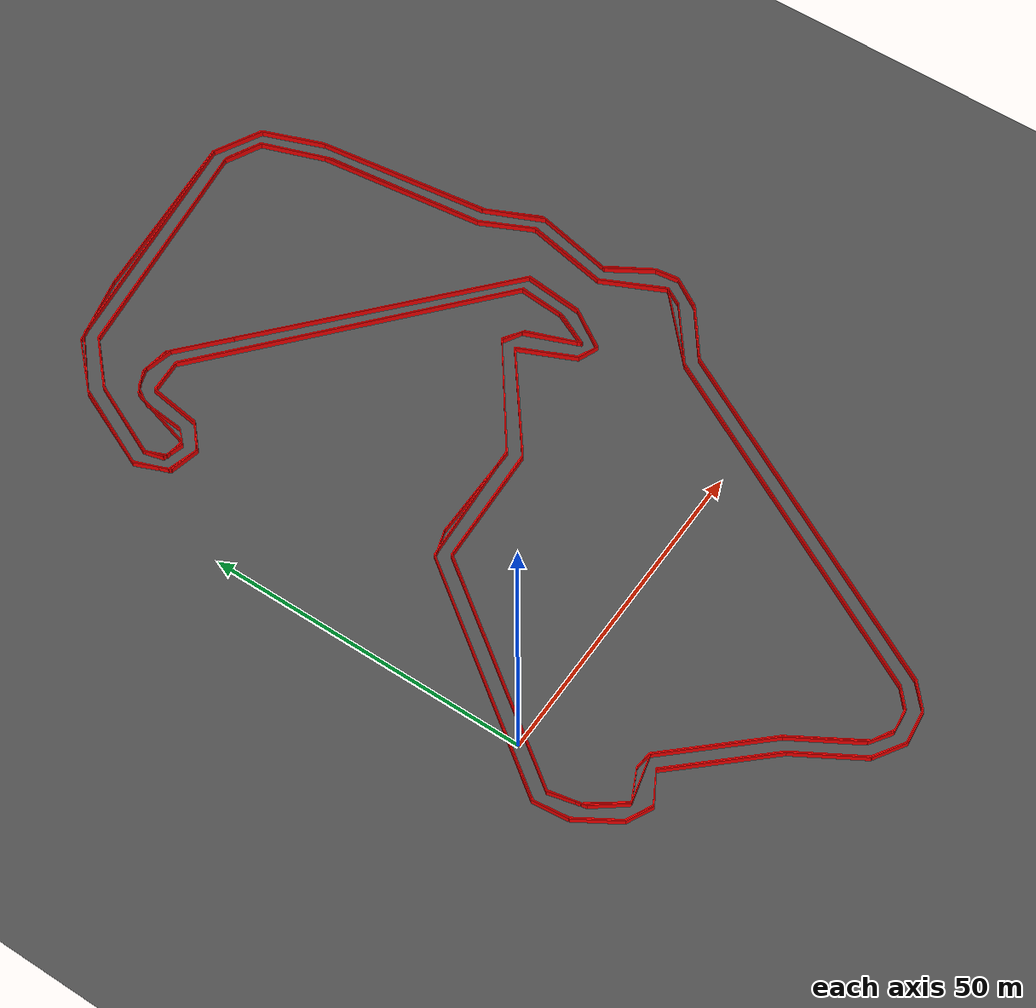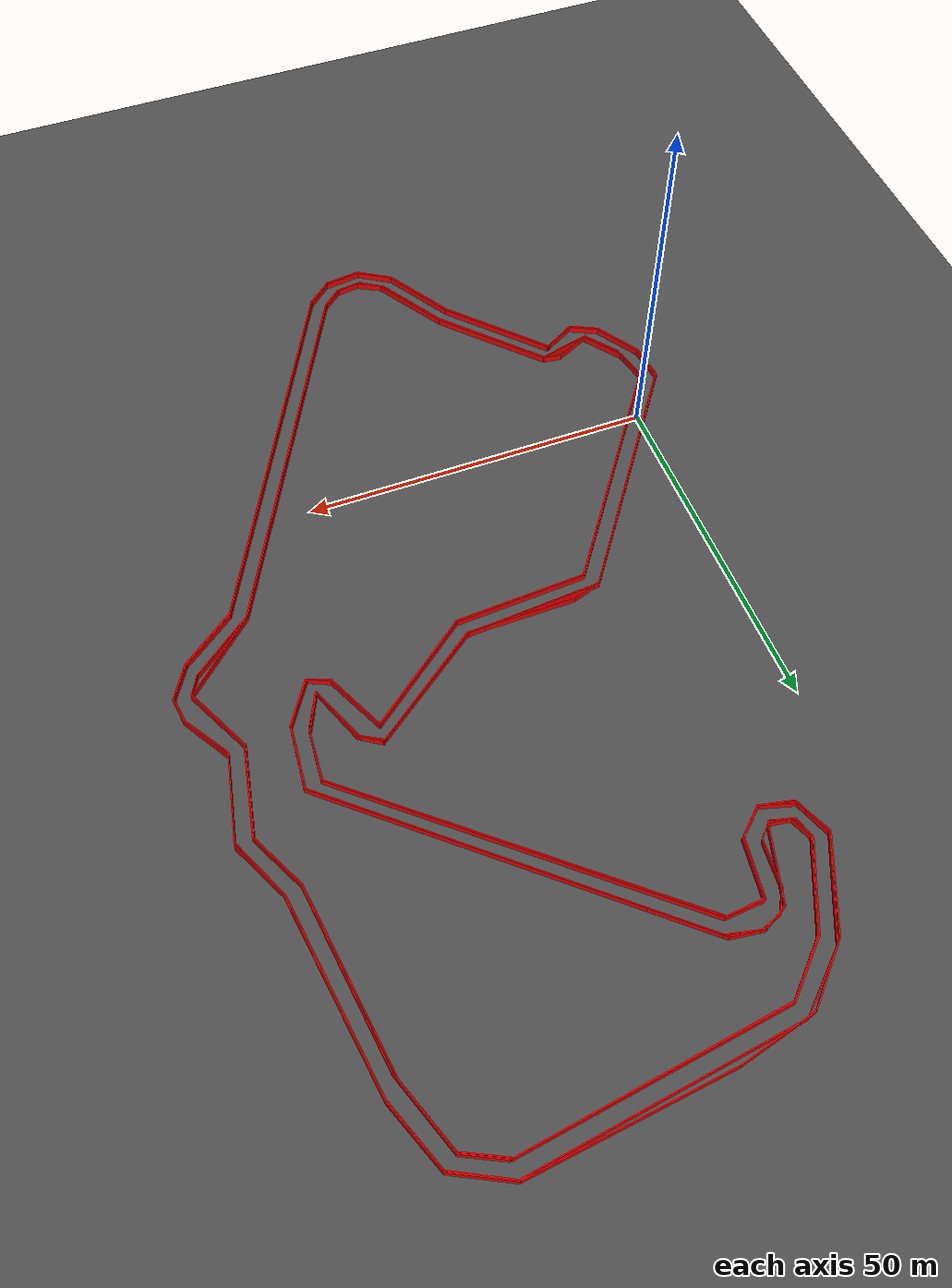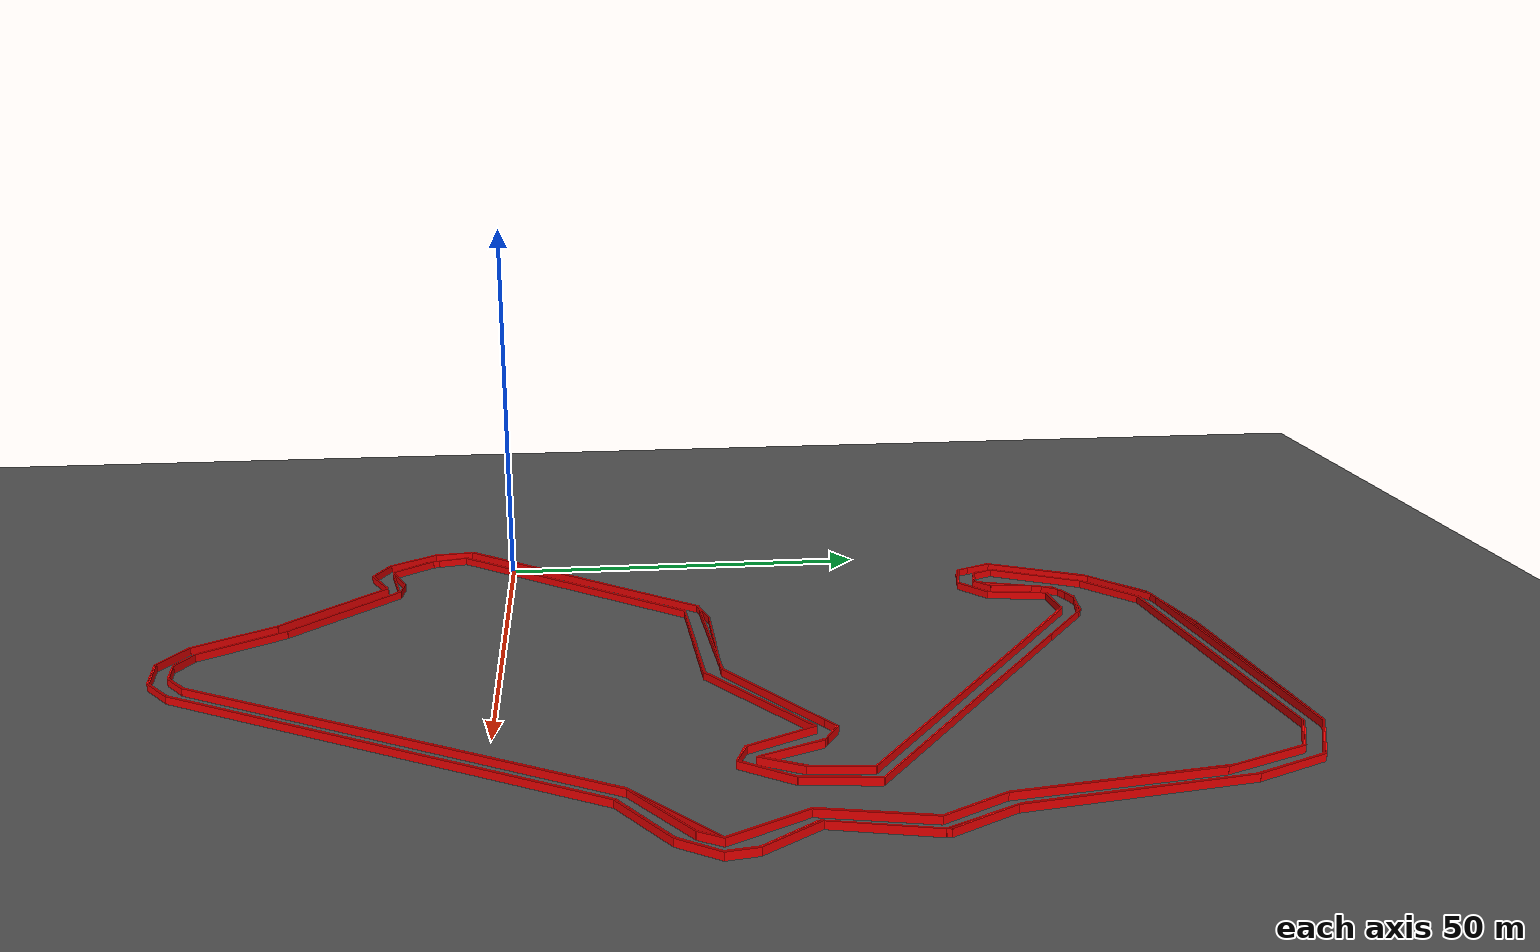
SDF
<?xml version="1.0" ?>
<sdf version="1.6">
  <world name="track_world">
    <scene>
      <ambient>0.4 0.4 0.4 1</ambient>
      <background>0.7 0.7 0.7 1</background>
      <shadows>true</shadows>
    </scene>
    <light name="sun" type="directional">
      <pose>0 0 10 0 0 0</pose>
      <diffuse>0.8 0.8 0.8 1</diffuse>
      <direction>-0.5 0.1 -0.9</direction>
    </light>
    <model name="ground_plane">
      <static>true</static>
      <link name="link">
        <collision name="collision">
          <geometry>
            <plane>
              <normal>0 0 1</normal>
              <size>1000 1000</size>
            </plane>
          </geometry>
        </collision>
        <visual name="visual">
          <geometry>
            <plane>
              <normal>0 0 1</normal>
              <size>1000 1000</size>
            </plane>
          </geometry>
          <material>
            <ambient>0.3 0.3 0.3 1</ambient>
            <diffuse>0.3 0.3 0.3 1</diffuse>
          </material>
        </visual>
      </link>
    </model>
    <model name="wall_0">
      <static>true</static>
      <pose>42.31821860208427 92.56603608975206 0.5 0 0 -3.037451008844692</pose>
      <link name="link">
        <visual name="visual">
          <geometry>
            <box>
              <size>27.449195399209803 0.15 1.0</size>
            </box>
          </geometry>
          <material>
            <ambient>1 0 0 1</ambient>
            <diffuse>1 0 0 1</diffuse>
          </material>
        </visual>
        <collision name="collision">
          <geometry>
            <box>
              <size>27.449195399209803 0.15 1.0</size>
            </box>
          </geometry>
        </collision>
      </link>
    </model>
    <model name="wall_1">
      <static>true</static>
      <pose>23.308138602084274 89.86683608975206 0.5 0 0 -2.908497981060588</pose>
      <link name="link">
        <visual name="visual">
          <geometry>
            <box>
              <size>11.017638617417065 0.15 1.0</size>
            </box>
          </geometry>
          <material>
            <ambient>1 0 0 1</ambient>
            <diffuse>1 0 0 1</diffuse>
          </material>
        </visual>
        <collision name="collision">
          <geometry>
            <box>
              <size>11.017638617417065 0.15 1.0</size>
            </box>
          </geometry>
        </collision>
      </link>
    </model>
    <model name="wall_2">
      <static>true</static>
      <pose>14.632138602084279 85.23963608975205 0.5 0 0 -2.350414207748683</pose>
      <link name="link">
        <visual name="visual">
          <geometry>
            <box>
              <size>9.434206574800024 0.15 1.0</size>
            </box>
          </geometry>
          <material>
            <ambient>1 0 0 1</ambient>
            <diffuse>1 0 0 1</diffuse>
          </material>
        </visual>
        <collision name="collision">
          <geometry>
            <box>
              <size>9.434206574800024 0.15 1.0</size>
            </box>
          </geometry>
        </collision>
      </link>
    </model>
    <model name="wall_3">
      <static>true</static>
      <pose>8.539658602084277 75.63819608975206 0.5 0 0 -1.9890206563741262</pose>
      <link name="link">
        <visual name="visual">
          <geometry>
            <box>
              <size>13.671790446141276 0.15 1.0</size>
            </box>
          </geometry>
          <material>
            <ambient>1 0 0 1</ambient>
            <diffuse>1 0 0 1</diffuse>
          </material>
        </visual>
        <collision name="collision">
          <geometry>
            <box>
              <size>13.671790446141276 0.15 1.0</size>
            </box>
          </geometry>
        </collision>
      </link>
    </model>
    <model name="wall_4">
      <static>true</static>
      <pose>6.843018602084275 66.80795608975205 0.5 0 0 -1.1749458854574806</pose>
      <link name="link">
        <visual name="visual">
          <geometry>
            <box>
              <size>5.600101603649705 0.15 1.0</size>
            </box>
          </geometry>
          <material>
            <ambient>1 0 0 1</ambient>
            <diffuse>1 0 0 1</diffuse>
          </material>
        </visual>
        <collision name="collision">
          <geometry>
            <box>
              <size>5.600101603649705 0.15 1.0</size>
            </box>
          </geometry>
        </collision>
      </link>
    </model>
    <model name="wall_5">
      <static>true</static>
      <pose>10.236298602084275 63.72315608975206 0.5 0 0 -0.21336864215180842</pose>
      <link name="link">
        <visual name="visual">
          <geometry>
            <box>
              <size>4.734565069106139 0.15 1.0</size>
            </box>
          </geometry>
          <material>
            <ambient>1 0 0 1</ambient>
            <diffuse>1 0 0 1</diffuse>
          </material>
        </visual>
        <collision name="collision">
          <geometry>
            <box>
              <size>4.734565069106139 0.15 1.0</size>
            </box>
          </geometry>
        </collision>
      </link>
    </model>
    <model name="wall_6">
      <static>true</static>
      <pose>14.323658602084276 64.84139608975207 0.5 0 0 0.739974883975872</pose>
      <link name="link">
        <visual name="visual">
          <geometry>
            <box>
              <size>4.803777500259563 0.15 1.0</size>
            </box>
          </geometry>
          <material>
            <ambient>1 0 0 1</ambient>
            <diffuse>1 0 0 1</diffuse>
          </material>
        </visual>
        <collision name="collision">
          <geometry>
            <box>
              <size>4.803777500259563 0.15 1.0</size>
            </box>
          </geometry>
        </collision>
      </link>
    </model>
    <model name="wall_7">
      <static>true</static>
      <pose>16.675818602084274 70.43259608975205 0.5 0 0 1.4261818875749566</pose>
      <link name="link">
        <visual name="visual">
          <geometry>
            <box>
              <size>8.027151071806234 0.15 1.0</size>
            </box>
          </geometry>
          <material>
            <ambient>1 0 0 1</ambient>
            <diffuse>1 0 0 1</diffuse>
          </material>
        </visual>
        <collision name="collision">
          <geometry>
            <box>
              <size>8.027151071806234 0.15 1.0</size>
            </box>
          </geometry>
        </collision>
      </link>
    </model>
    <model name="wall_8">
      <static>true</static>
      <pose>19.837738602084272 74.63563608975207 0.5 0 0 0.08931399299322305</pose>
      <link name="link">
        <visual name="visual">
          <geometry>
            <box>
              <size>5.187717432551623 0.15 1.0</size>
            </box>
          </geometry>
          <material>
            <ambient>1 0 0 1</ambient>
            <diffuse>1 0 0 1</diffuse>
          </material>
        </visual>
        <collision name="collision">
          <geometry>
            <box>
              <size>5.187717432551623 0.15 1.0</size>
            </box>
          </geometry>
        </collision>
      </link>
    </model>
    <model name="wall_9">
      <static>true</static>
      <pose>41.81693860208427 58.09339608975206 0.5 0 0 -0.7130300929492385</pose>
      <link name="link">
        <visual name="visual">
          <geometry>
            <box>
              <size>51.285321862006484 0.15 1.0</size>
            </box>
          </geometry>
          <material>
            <ambient>1 0 0 1</ambient>
            <diffuse>1 0 0 1</diffuse>
          </material>
        </visual>
        <collision name="collision">
          <geometry>
            <box>
              <size>51.285321862006484 0.15 1.0</size>
            </box>
          </geometry>
        </collision>
      </link>
    </model>
    <model name="wall_10">
      <static>true</static>
      <pose>60.94269860208427 37.84939608975206 0.5 0 0 -1.6484178355322898</pose>
      <link name="link">
        <visual name="visual">
          <geometry>
            <box>
              <size>6.9617621236006 0.15 1.0</size>
            </box>
          </geometry>
          <material>
            <ambient>1 0 0 1</ambient>
            <diffuse>1 0 0 1</diffuse>
          </material>
        </visual>
        <collision name="collision">
          <geometry>
            <box>
              <size>6.9617621236006 0.15 1.0</size>
            </box>
          </geometry>
        </collision>
      </link>
    </model>
    <model name="wall_11">
      <static>true</static>
      <pose>59.40029860208427 31.67979608975206 0.5 0 0 -2.0113266674114096</pose>
      <link name="link">
        <visual name="visual">
          <geometry>
            <box>
              <size>5.968211119054026 0.15 1.0</size>
            </box>
          </geometry>
          <material>
            <ambient>1 0 0 1</ambient>
            <diffuse>1 0 0 1</diffuse>
          </material>
        </visual>
        <collision name="collision">
          <geometry>
            <box>
              <size>5.968211119054026 0.15 1.0</size>
            </box>
          </geometry>
        </collision>
      </link>
    </model>
    <model name="wall_12">
      <static>true</static>
      <pose>56.70109860208427 32.87515608975206 0.5 0 0 1.9219501693955425</pose>
      <link name="link">
        <visual name="visual">
          <geometry>
            <box>
              <size>8.295330626804462 0.15 1.0</size>
            </box>
          </geometry>
          <material>
            <ambient>1 0 0 1</ambient>
            <diffuse>1 0 0 1</diffuse>
          </material>
        </visual>
        <collision name="collision">
          <geometry>
            <box>
              <size>8.295330626804462 0.15 1.0</size>
            </box>
          </geometry>
        </collision>
      </link>
    </model>
    <model name="wall_13">
      <static>true</static>
      <pose>53.809098602084276 37.77227608975206 0.5 0 0 2.5415424401880418</pose>
      <link name="link">
        <visual name="visual">
          <geometry>
            <box>
              <size>3.5508714603601135 0.15 1.0</size>
            </box>
          </geometry>
          <material>
            <ambient>1 0 0 1</ambient>
            <diffuse>1 0 0 1</diffuse>
          </material>
        </visual>
        <collision name="collision">
          <geometry>
            <box>
              <size>3.5508714603601135 0.15 1.0</size>
            </box>
          </geometry>
        </collision>
      </link>
    </model>
    <model name="wall_14">
      <static>true</static>
      <pose>44.55469860208427 33.02939608975206 0.5 0 0 -2.506059503658031</pose>
      <link name="link">
        <visual name="visual">
          <geometry>
            <box>
              <size>19.357734492238496 0.15 1.0</size>
            </box>
          </geometry>
          <material>
            <ambient>1 0 0 1</ambient>
            <diffuse>1 0 0 1</diffuse>
          </material>
        </visual>
        <collision name="collision">
          <geometry>
            <box>
              <size>19.357734492238496 0.15 1.0</size>
            </box>
          </geometry>
        </collision>
      </link>
    </model>
    <model name="wall_15">
      <static>true</static>
      <pose>27.04845860208427 26.589876089752067 0.5 0 0 -3.070285188804503</pose>
      <link name="link">
        <visual name="visual">
          <geometry>
            <box>
              <size>19.483754067509675 0.15 1.0</size>
            </box>
          </geometry>
          <material>
            <ambient>1 0 0 1</ambient>
            <diffuse>1 0 0 1</diffuse>
          </material>
        </visual>
        <collision name="collision">
          <geometry>
            <box>
              <size>19.483754067509675 0.15 1.0</size>
            </box>
          </geometry>
        </collision>
      </link>
    </model>
    <model name="wall_16">
      <static>true</static>
      <pose>5.724778602084275 9.893396089752066 0.5 0 0 -2.198301921255311</pose>
      <link name="link">
        <visual name="visual">
          <geometry>
            <box>
              <size>39.536769761506825 0.15 1.0</size>
            </box>
          </geometry>
          <material>
            <ambient>1 0 0 1</ambient>
            <diffuse>1 0 0 1</diffuse>
          </material>
        </visual>
        <collision name="collision">
          <geometry>
            <box>
              <size>39.536769761506825 0.15 1.0</size>
            </box>
          </geometry>
        </collision>
      </link>
    </model>
    <model name="wall_17">
      <static>true</static>
      <pose>-5.611861397915725 -8.885323910247937 0.5 0 0 -1.473878699000534</pose>
      <link name="link">
        <visual name="visual">
          <geometry>
            <box>
              <size>5.578820502149181 0.15 1.0</size>
            </box>
          </geometry>
          <material>
            <ambient>1 0 0 1</ambient>
            <diffuse>1 0 0 1</diffuse>
          </material>
        </visual>
        <collision name="collision">
          <geometry>
            <box>
              <size>5.578820502149181 0.15 1.0</size>
            </box>
          </geometry>
        </collision>
      </link>
    </model>
    <model name="wall_18">
      <static>true</static>
      <pose>-3.4139413979157247 -14.785003910247937 0.5 0 0 -1.0177648826442556</pose>
      <link name="link">
        <visual name="visual">
          <geometry>
            <box>
              <size>7.340997667783308 0.15 1.0</size>
            </box>
          </geometry>
          <material>
            <ambient>1 0 0 1</ambient>
            <diffuse>1 0 0 1</diffuse>
          </material>
        </visual>
        <collision name="collision">
          <geometry>
            <box>
              <size>7.340997667783308 0.15 1.0</size>
            </box>
          </geometry>
        </collision>
      </link>
    </model>
    <model name="wall_19">
      <static>true</static>
      <pose>0.44205860208427694 -18.872363910247934 0.5 0 0 -0.46364760900080537</pose>
      <link name="link">
        <visual name="visual">
          <geometry>
            <box>
              <size>4.3111390606195945 0.15 1.0</size>
            </box>
          </geometry>
          <material>
            <ambient>1 0 0 1</ambient>
            <diffuse>1 0 0 1</diffuse>
          </material>
        </visual>
        <collision name="collision">
          <geometry>
            <box>
              <size>4.3111390606195945 0.15 1.0</size>
            </box>
          </geometry>
        </collision>
      </link>
    </model>
    <model name="wall_20">
      <static>true</static>
      <pose>4.683658602084275 -18.486763910247934 0.5 0 0 0.5280744484263598</pose>
      <link name="link">
        <visual name="visual">
          <geometry>
            <box>
              <size>5.3569264023318395 0.15 1.0</size>
            </box>
          </geometry>
          <material>
            <ambient>1 0 0 1</ambient>
            <diffuse>1 0 0 1</diffuse>
          </material>
        </visual>
        <collision name="collision">
          <geometry>
            <box>
              <size>5.3569264023318395 0.15 1.0</size>
            </box>
          </geometry>
        </collision>
      </link>
    </model>
    <model name="wall_21">
      <static>true</static>
      <pose>12.896938602084273 -23.538123910247933 0.5 0 0 -0.8261279770695137</pose>
      <link name="link">
        <visual name="visual">
          <geometry>
            <box>
              <size>17.410170938161407 0.15 1.0</size>
            </box>
          </geometry>
          <material>
            <ambient>1 0 0 1</ambient>
            <diffuse>1 0 0 1</diffuse>
          </material>
        </visual>
        <collision name="collision">
          <geometry>
            <box>
              <size>17.410170938161407 0.15 1.0</size>
            </box>
          </geometry>
        </collision>
      </link>
    </model>
    <model name="wall_22">
      <static>true</static>
      <pose>21.650058602084272 -34.75908391024793 0.5 0 0 -1.0362799456764245</pose>
      <link name="link">
        <visual name="visual">
          <geometry>
            <box>
              <size>11.202592527375078 0.15 1.0</size>
            </box>
          </geometry>
          <material>
            <ambient>1 0 0 1</ambient>
            <diffuse>1 0 0 1</diffuse>
          </material>
        </visual>
        <collision name="collision">
          <geometry>
            <box>
              <size>11.202592527375078 0.15 1.0</size>
            </box>
          </geometry>
        </collision>
      </link>
    </model>
    <model name="wall_23">
      <static>true</static>
      <pose>26.817098602084272 -41.005803910247934 0.5 0 0 -0.5525843502907148</pose>
      <link name="link">
        <visual name="visual">
          <geometry>
            <box>
              <size>5.436276269065071 0.15 1.0</size>
            </box>
          </geometry>
          <material>
            <ambient>1 0 0 1</ambient>
            <diffuse>1 0 0 1</diffuse>
          </material>
        </visual>
        <collision name="collision">
          <geometry>
            <box>
              <size>5.436276269065071 0.15 1.0</size>
            </box>
          </geometry>
        </collision>
      </link>
    </model>
    <model name="wall_24">
      <static>true</static>
      <pose>31.675658602084276 -42.124043910247934 0.5 0 0 0.12062366858010372</pose>
      <link name="link">
        <visual name="visual">
          <geometry>
            <box>
              <size>5.127175172353689 0.15 1.0</size>
            </box>
          </geometry>
          <material>
            <ambient>1 0 0 1</ambient>
            <diffuse>1 0 0 1</diffuse>
          </material>
        </visual>
        <collision name="collision">
          <geometry>
            <box>
              <size>5.127175172353689 0.15 1.0</size>
            </box>
          </geometry>
        </collision>
      </link>
    </model>
    <model name="wall_25">
      <static>true</static>
      <pose>36.03293860208428 -40.234603910247934 0.5 0 0 0.7173217051394482</pose>
      <link name="link">
        <visual name="visual">
          <geometry>
            <box>
              <size>4.809963951632066 0.15 1.0</size>
            </box>
          </geometry>
          <material>
            <ambient>1 0 0 1</ambient>
            <diffuse>1 0 0 1</diffuse>
          </material>
        </visual>
        <collision name="collision">
          <geometry>
            <box>
              <size>4.809963951632066 0.15 1.0</size>
            </box>
          </geometry>
        </collision>
      </link>
    </model>
    <model name="wall_26">
      <static>true</static>
      <pose>51.611178602084266 -12.664203910247934 0.5 0 0 1.0836926099479667</pose>
      <link name="link">
        <visual name="visual">
          <geometry>
            <box>
              <size>58.8201171355515 0.15 1.0</size>
            </box>
          </geometry>
          <material>
            <ambient>1 0 0 1</ambient>
            <diffuse>1 0 0 1</diffuse>
          </material>
        </visual>
        <collision name="collision">
          <geometry>
            <box>
              <size>58.8201171355515 0.15 1.0</size>
            </box>
          </geometry>
        </collision>
      </link>
    </model>
    <model name="wall_27">
      <static>true</static>
      <pose>69.11741860208427 16.140116089752063 0.5 0 0 0.6451485537608409</pose>
      <link name="link">
        <visual name="visual">
          <geometry>
            <box>
              <size>9.362380705098476 0.15 1.0</size>
            </box>
          </geometry>
          <material>
            <ambient>1 0 0 1</ambient>
            <diffuse>1 0 0 1</diffuse>
          </material>
        </visual>
        <collision name="collision">
          <geometry>
            <box>
              <size>9.362380705098476 0.15 1.0</size>
            </box>
          </geometry>
        </collision>
      </link>
    </model>
    <model name="wall_28">
      <static>true</static>
      <pose>74.24589860208428 21.26859608975206 0.5 0 0 1.030376826524313</pose>
      <link name="link">
        <visual name="visual">
          <geometry>
            <box>
              <size>5.3961961215656356 0.15 1.0</size>
            </box>
          </geometry>
          <material>
            <ambient>1 0 0 1</ambient>
            <diffuse>1 0 0 1</diffuse>
          </material>
        </visual>
        <collision name="collision">
          <geometry>
            <box>
              <size>5.3961961215656356 0.15 1.0</size>
            </box>
          </geometry>
        </collision>
      </link>
    </model>
    <model name="wall_29">
      <static>true</static>
      <pose>75.40269860208427 25.39451608975206 0.5 0 0 1.6977691164089805</pose>
      <link name="link">
        <visual name="visual">
          <geometry>
            <box>
              <size>3.6540559557839303 0.15 1.0</size>
            </box>
          </geometry>
          <material>
            <ambient>1 0 0 1</ambient>
            <diffuse>1 0 0 1</diffuse>
          </material>
        </visual>
        <collision name="collision">
          <geometry>
            <box>
              <size>3.6540559557839303 0.15 1.0</size>
            </box>
          </geometry>
        </collision>
      </link>
    </model>
    <model name="wall_30">
      <static>true</static>
      <pose>73.16621860208427 30.56155608975206 0.5 0 0 2.1095237813029404</pose>
      <link name="link">
        <visual name="visual">
          <geometry>
            <box>
              <size>7.816559983215114 0.15 1.0</size>
            </box>
          </geometry>
          <material>
            <ambient>1 0 0 1</ambient>
            <diffuse>1 0 0 1</diffuse>
          </material>
        </visual>
        <collision name="collision">
          <geometry>
            <box>
              <size>7.816559983215114 0.15 1.0</size>
            </box>
          </geometry>
        </collision>
      </link>
    </model>
    <model name="wall_31">
      <static>true</static>
      <pose>72.47213860208427 40.04731608975206 0.5 0 0 1.3601325468103365</pose>
      <link name="link">
        <visual name="visual">
          <geometry>
            <box>
              <size>12.539294615439891 0.15 1.0</size>
            </box>
          </geometry>
          <material>
            <ambient>1 0 0 1</ambient>
            <diffuse>1 0 0 1</diffuse>
          </material>
        </visual>
        <collision name="collision">
          <geometry>
            <box>
              <size>12.539294615439891 0.15 1.0</size>
            </box>
          </geometry>
        </collision>
      </link>
    </model>
    <model name="wall_32">
      <static>true</static>
      <pose>71.93229860208427 50.11147608975206 0.5 0 0 2.0106389096106305</pose>
      <link name="link">
        <visual name="visual">
          <geometry>
            <box>
              <size>8.693719505206039 0.15 1.0</size>
            </box>
          </geometry>
          <material>
            <ambient>1 0 0 1</ambient>
            <diffuse>1 0 0 1</diffuse>
          </material>
        </visual>
        <collision name="collision">
          <geometry>
            <box>
              <size>8.693719505206039 0.15 1.0</size>
            </box>
          </geometry>
        </collision>
      </link>
    </model>
    <model name="wall_33">
      <static>true</static>
      <pose>68.34621860208428 67.61771608975207 0.5 0 0 1.697947539150035</pose>
      <link name="link">
        <visual name="visual">
          <geometry>
            <box>
              <size>27.36717052049043 0.15 1.0</size>
            </box>
          </geometry>
          <material>
            <ambient>1 0 0 1</ambient>
            <diffuse>1 0 0 1</diffuse>
          </material>
        </visual>
        <collision name="collision">
          <geometry>
            <box>
              <size>27.36717052049043 0.15 1.0</size>
            </box>
          </geometry>
        </collision>
      </link>
    </model>
    <model name="wall_34">
      <static>true</static>
      <pose>64.91437860208427 85.74091608975206 0.5 0 0 1.9277082631465672</pose>
      <link name="link">
        <visual name="visual">
          <geometry>
            <box>
              <size>9.712222257753359 0.15 1.0</size>
            </box>
          </geometry>
          <material>
            <ambient>1 0 0 1</ambient>
            <diffuse>1 0 0 1</diffuse>
          </material>
        </visual>
        <collision name="collision">
          <geometry>
            <box>
              <size>9.712222257753359 0.15 1.0</size>
            </box>
          </geometry>
        </collision>
      </link>
    </model>
    <model name="wall_35">
      <static>true</static>
      <pose>59.593098602084275 92.14187608975206 0.5 0 0 2.6694706711860157</pose>
      <link name="link">
        <visual name="visual">
          <geometry>
            <box>
              <size>8.13972282181648 0.15 1.0</size>
            </box>
          </geometry>
          <material>
            <ambient>1 0 0 1</ambient>
            <diffuse>1 0 0 1</diffuse>
          </material>
        </visual>
        <collision name="collision">
          <geometry>
            <box>
              <size>8.13972282181648 0.15 1.0</size>
            </box>
          </geometry>
        </collision>
      </link>
    </model>
    <model name="wall_36">
      <static>true</static>
      <pose>59.59309860208427 91.98763608975206 0.5 0 0 -0.4808872801953336</pose>
      <link name="link">
        <visual name="visual">
          <geometry>
            <box>
              <size>8.002663287881091 0.15 1.0</size>
            </box>
          </geometry>
          <material>
            <ambient>1 0 0 1</ambient>
            <diffuse>1 0 0 1</diffuse>
          </material>
        </visual>
        <collision name="collision">
          <geometry>
            <box>
              <size>8.002663287881091 0.15 1.0</size>
            </box>
          </geometry>
        </collision>
      </link>
    </model>
    <model name="wall_37">
      <static>true</static>
      <pose>64.83725860208426 85.54811608975206 0.5 0 0 -1.2166381699386704</pose>
      <link name="link">
        <visual name="visual">
          <geometry>
            <box>
              <size>9.784519270602948 0.15 1.0</size>
            </box>
          </geometry>
          <material>
            <ambient>1 0 0 1</ambient>
            <diffuse>1 0 0 1</diffuse>
          </material>
        </visual>
        <collision name="collision">
          <geometry>
            <box>
              <size>9.784519270602948 0.15 1.0</size>
            </box>
          </geometry>
        </collision>
      </link>
    </model>
    <model name="wall_38">
      <static>true</static>
      <pose>68.19197860208426 67.69483608975204 0.5 0 0 -1.4464413322481353</pose>
      <link name="link">
        <visual name="visual">
          <geometry>
            <box>
              <size>26.735736654597705 0.15 1.0</size>
            </box>
          </geometry>
          <material>
            <ambient>1 0 0 1</ambient>
            <diffuse>1 0 0 1</diffuse>
          </material>
        </visual>
        <collision name="collision">
          <geometry>
            <box>
              <size>26.735736654597705 0.15 1.0</size>
            </box>
          </geometry>
        </collision>
      </link>
    </model>
    <model name="wall_39">
      <static>true</static>
      <pose>71.77805860208427 50.03435608975206 0.5 0 0 -1.1574659222555665</pose>
      <link name="link">
        <visual name="visual">
          <geometry>
            <box>
              <size>9.60012360453761 0.15 1.0</size>
            </box>
          </geometry>
          <material>
            <ambient>1 0 0 1</ambient>
            <diffuse>1 0 0 1</diffuse>
          </material>
        </visual>
        <collision name="collision">
          <geometry>
            <box>
              <size>9.60012360453761 0.15 1.0</size>
            </box>
          </geometry>
        </collision>
      </link>
    </model>
    <model name="wall_40">
      <static>true</static>
      <pose>72.39501860208428 39.58459608975206 0.5 0 0 -1.7840635696365683</pose>
      <link name="link">
        <visual name="visual">
          <geometry>
            <box>
              <size>12.388506487547236 0.15 1.0</size>
            </box>
          </geometry>
          <material>
            <ambient>1 0 0 1</ambient>
            <diffuse>1 0 0 1</diffuse>
          </material>
        </visual>
        <collision name="collision">
          <geometry>
            <box>
              <size>12.388506487547236 0.15 1.0</size>
            </box>
          </geometry>
        </collision>
      </link>
    </model>
    <model name="wall_41">
      <static>true</static>
      <pose>73.05053860208427 30.36875608975206 0.5 0 0 -1.0143923976059468</pose>
      <link name="link">
        <visual name="visual">
          <geometry>
            <box>
              <size>7.447172972343268 0.15 1.0</size>
            </box>
          </geometry>
          <material>
            <ambient>1 0 0 1</ambient>
            <diffuse>1 0 0 1</diffuse>
          </material>
        </visual>
        <collision name="collision">
          <geometry>
            <box>
              <size>7.447172972343268 0.15 1.0</size>
            </box>
          </geometry>
        </collision>
      </link>
    </model>
    <model name="wall_42">
      <static>true</static>
      <pose>75.24845860208427 25.355956089752063 0.5 0 0 -1.4464413322481375</pose>
      <link name="link">
        <visual name="visual">
          <geometry>
            <box>
              <size>3.7305679052926966 0.15 1.0</size>
            </box>
          </geometry>
          <material>
            <ambient>1 0 0 1</ambient>
            <diffuse>1 0 0 1</diffuse>
          </material>
        </visual>
        <collision name="collision">
          <geometry>
            <box>
              <size>3.7305679052926966 0.15 1.0</size>
            </box>
          </geometry>
        </collision>
      </link>
    </model>
    <model name="wall_43">
      <static>true</static>
      <pose>74.09165860208427 21.268596089752066 0.5 0 0 -2.12629006206044</pose>
      <link name="link">
        <visual name="visual">
          <geometry>
            <box>
              <size>5.264534538209432 0.15 1.0</size>
            </box>
          </geometry>
          <material>
            <ambient>1 0 0 1</ambient>
            <diffuse>1 0 0 1</diffuse>
          </material>
        </visual>
        <collision name="collision">
          <geometry>
            <box>
              <size>5.264534538209432 0.15 1.0</size>
            </box>
          </geometry>
        </collision>
      </link>
    </model>
    <model name="wall_44">
      <static>true</static>
      <pose>69.00173860208427 16.255796089752067 0.5 0 0 -2.4980915447965084</pose>
      <link name="link">
        <visual name="visual">
          <geometry>
            <box>
              <size>9.254399999999986 0.15 1.0</size>
            </box>
          </geometry>
          <material>
            <ambient>1 0 0 1</ambient>
            <diffuse>1 0 0 1</diffuse>
          </material>
        </visual>
        <collision name="collision">
          <geometry>
            <box>
              <size>9.254399999999986 0.15 1.0</size>
            </box>
          </geometry>
        </collision>
      </link>
    </model>
    <model name="wall_45">
      <static>true</static>
      <pose>51.53405860208427 -12.509963910247933 0.5 0 0 -2.057900043641827</pose>
      <link name="link">
        <visual name="visual">
          <geometry>
            <box>
              <size>58.82011713555151 0.15 1.0</size>
            </box>
          </geometry>
          <material>
            <ambient>1 0 0 1</ambient>
            <diffuse>1 0 0 1</diffuse>
          </material>
        </visual>
        <collision name="collision">
          <geometry>
            <box>
              <size>58.82011713555151 0.15 1.0</size>
            </box>
          </geometry>
        </collision>
      </link>
    </model>
    <model name="wall_46">
      <static>true</static>
      <pose>36.071498602084276 -40.041803910247936 0.5 0 0 -2.403777593469327</pose>
      <link name="link">
        <visual name="visual">
          <geometry>
            <box>
              <size>4.585884887172806 0.15 1.0</size>
            </box>
          </geometry>
          <material>
            <ambient>1 0 0 1</ambient>
            <diffuse>1 0 0 1</diffuse>
          </material>
        </visual>
        <collision name="collision">
          <geometry>
            <box>
              <size>4.585884887172806 0.15 1.0</size>
            </box>
          </geometry>
        </collision>
      </link>
    </model>
    <model name="wall_47">
      <static>true</static>
      <pose>31.71421860208428 -41.931243910247936 0.5 0 0 -3.0118901164338814</pose>
      <link name="link">
        <visual name="visual">
          <geometry>
            <box>
              <size>5.366355176914776 0.15 1.0</size>
            </box>
          </geometry>
          <material>
            <ambient>1 0 0 1</ambient>
            <diffuse>1 0 0 1</diffuse>
          </material>
        </visual>
        <collision name="collision">
          <geometry>
            <box>
              <size>5.366355176914776 0.15 1.0</size>
            </box>
          </geometry>
        </collision>
      </link>
    </model>
    <model name="wall_48">
      <static>true</static>
      <pose>26.81709860208428 -40.85156391024793 0.5 0 0 2.573748609326352</pose>
      <link name="link">
        <visual name="visual">
          <geometry>
            <box>
              <size>5.305609389617751 0.15 1.0</size>
            </box>
          </geometry>
          <material>
            <ambient>1 0 0 1</ambient>
            <diffuse>1 0 0 1</diffuse>
          </material>
        </visual>
        <collision name="collision">
          <geometry>
            <box>
              <size>5.305609389617751 0.15 1.0</size>
            </box>
          </geometry>
        </collision>
      </link>
    </model>
    <model name="wall_49">
      <static>true</static>
      <pose>21.727178602084276 -34.604843910247936 0.5 0 0 2.1053127079133693</pose>
      <link name="link">
        <visual name="visual">
          <geometry>
            <box>
              <size>11.202592527375078 0.15 1.0</size>
            </box>
          </geometry>
          <material>
            <ambient>1 0 0 1</ambient>
            <diffuse>1 0 0 1</diffuse>
          </material>
        </visual>
        <collision name="collision">
          <geometry>
            <box>
              <size>11.202592527375078 0.15 1.0</size>
            </box>
          </geometry>
        </collision>
      </link>
    </model>
    <model name="wall_50">
      <static>true</static>
      <pose>13.012618602084274 -23.422443910247935 0.5 0 0 2.3152079928786398</pose>
      <link name="link">
        <visual name="visual">
          <geometry>
            <box>
              <size>17.301197809909002 0.15 1.0</size>
            </box>
          </geometry>
          <material>
            <ambient>1 0 0 1</ambient>
            <diffuse>1 0 0 1</diffuse>
          </material>
        </visual>
        <collision name="collision">
          <geometry>
            <box>
              <size>17.301197809909002 0.15 1.0</size>
            </box>
          </geometry>
        </collision>
      </link>
    </model>
    <model name="wall_51">
      <static>true</static>
      <pose>4.799338602084276 -18.371083910247936 0.5 0 0 -2.633103329510102</pose>
      <link name="link">
        <visual name="visual">
          <geometry>
            <box>
              <size>5.385715383196552 0.15 1.0</size>
            </box>
          </geometry>
          <material>
            <ambient>1 0 0 1</ambient>
            <diffuse>1 0 0 1</diffuse>
          </material>
        </visual>
        <collision name="collision">
          <geometry>
            <box>
              <size>5.385715383196552 0.15 1.0</size>
            </box>
          </geometry>
        </collision>
      </link>
    </model>
    <model name="wall_52">
      <static>true</static>
      <pose>0.5191786020842777 -18.718123910247936 0.5 0 0 2.6779450445889865</pose>
      <link name="link">
        <visual name="visual">
          <geometry>
            <box>
              <size>4.311139060619598 0.15 1.0</size>
            </box>
          </geometry>
          <material>
            <ambient>1 0 0 1</ambient>
            <diffuse>1 0 0 1</diffuse>
          </material>
        </visual>
        <collision name="collision">
          <geometry>
            <box>
              <size>4.311139060619598 0.15 1.0</size>
            </box>
          </geometry>
        </collision>
      </link>
    </model>
    <model name="wall_53">
      <static>true</static>
      <pose>-3.2982613979157236 -14.707883910247936 0.5 0 0 2.1259749029155017</pose>
      <link name="link">
        <visual name="visual">
          <geometry>
            <box>
              <size>7.169257046919154 0.15 1.0</size>
            </box>
          </geometry>
          <material>
            <ambient>1 0 0 1</ambient>
            <diffuse>1 0 0 1</diffuse>
          </material>
        </visual>
        <collision name="collision">
          <geometry>
            <box>
              <size>7.169257046919154 0.15 1.0</size>
            </box>
          </geometry>
        </collision>
      </link>
    </model>
    <model name="wall_54">
      <static>true</static>
      <pose>-5.4961813979157235 -9.001003910247938 0.5 0 0 1.686222987161821</pose>
      <link name="link">
        <visual name="visual">
          <geometry>
            <box>
              <size>5.356926402331846 0.15 1.0</size>
            </box>
          </geometry>
          <material>
            <ambient>1 0 0 1</ambient>
            <diffuse>1 0 0 1</diffuse>
          </material>
        </visual>
        <collision name="collision">
          <geometry>
            <box>
              <size>5.356926402331846 0.15 1.0</size>
            </box>
          </geometry>
        </collision>
      </link>
    </model>
    <model name="wall_55">
      <static>true</static>
      <pose>5.724778602084275 9.66203608975206 0.5 0 0 0.9464559545421241</pose>
      <link name="link">
        <visual name="visual">
          <geometry>
            <box>
              <size>39.44640883394076 0.15 1.0</size>
            </box>
          </geometry>
          <material>
            <ambient>1 0 0 1</ambient>
            <diffuse>1 0 0 1</diffuse>
          </material>
        </visual>
        <collision name="collision">
          <geometry>
            <box>
              <size>39.44640883394076 0.15 1.0</size>
            </box>
          </geometry>
        </collision>
      </link>
    </model>
    <model name="wall_56">
      <static>true</static>
      <pose>19.25933860208427 26.31995608975206 0.5 0 0 0.315970271952982</pose>
      <link name="link">
        <visual name="visual">
          <geometry>
            <box>
              <size>4.21910544300566 0.15 1.0</size>
            </box>
          </geometry>
          <material>
            <ambient>1 0 0 1</ambient>
            <diffuse>1 0 0 1</diffuse>
          </material>
        </visual>
        <collision name="collision">
          <geometry>
            <box>
              <size>4.21910544300566 0.15 1.0</size>
            </box>
          </geometry>
        </collision>
      </link>
    </model>
    <model name="wall_57">
      <static>true</static>
      <pose>29.015018602084268 27.052596089752065 0.5 0 0 0.009949920392805265</pose>
      <link name="link">
        <visual name="visual">
          <geometry>
            <box>
              <size>15.501887344191351 0.15 1.0</size>
            </box>
          </geometry>
          <material>
            <ambient>1 0 0 1</ambient>
            <diffuse>1 0 0 1</diffuse>
          </material>
        </visual>
        <collision name="collision">
          <geometry>
            <box>
              <size>15.501887344191351 0.15 1.0</size>
            </box>
          </geometry>
        </collision>
      </link>
    </model>
    <model name="wall_58">
      <static>true</static>
      <pose>44.43901860208427 32.87515608975206 0.5 0 0 0.6426966037375662</pose>
      <link name="link">
        <visual name="visual">
          <geometry>
            <box>
              <size>19.172038204343316 0.15 1.0</size>
            </box>
          </geometry>
          <material>
            <ambient>1 0 0 1</ambient>
            <diffuse>1 0 0 1</diffuse>
          </material>
        </visual>
        <collision name="collision">
          <geometry>
            <box>
              <size>19.172038204343316 0.15 1.0</size>
            </box>
          </geometry>
        </collision>
      </link>
    </model>
    <model name="wall_59">
      <static>true</static>
      <pose>53.53917860208427 37.81083608975206 0.5 0 0 -0.5162306706117454</pose>
      <link name="link">
        <visual name="visual">
          <geometry>
            <box>
              <size>3.2810005888448144 0.15 1.0</size>
            </box>
          </geometry>
          <material>
            <ambient>1 0 0 1</ambient>
            <diffuse>1 0 0 1</diffuse>
          </material>
        </visual>
        <collision name="collision">
          <geometry>
            <box>
              <size>3.2810005888448144 0.15 1.0</size>
            </box>
          </geometry>
        </collision>
      </link>
    </model>
    <model name="wall_60">
      <static>true</static>
      <pose>56.585418602084275 32.913716089752064 0.5 0 0 -1.1935472671525371</pose>
      <link name="link">
        <visual name="visual">
          <geometry>
            <box>
              <size>8.793032878364547 0.15 1.0</size>
            </box>
          </geometry>
          <material>
            <ambient>1 0 0 1</ambient>
            <diffuse>1 0 0 1</diffuse>
          </material>
        </visual>
        <collision name="collision">
          <geometry>
            <box>
              <size>8.793032878364547 0.15 1.0</size>
            </box>
          </geometry>
        </collision>
      </link>
    </model>
    <model name="wall_61">
      <static>true</static>
      <pose>59.438858602084274 31.332756089752067 0.5 0 0 1.1133214788988721</pose>
      <link name="link">
        <visual name="visual">
          <geometry>
            <box>
              <size>5.58734266942703 0.15 1.0</size>
            </box>
          </geometry>
          <material>
            <ambient>1 0 0 1</ambient>
            <diffuse>1 0 0 1</diffuse>
          </material>
        </visual>
        <collision name="collision">
          <geometry>
            <box>
              <size>5.58734266942703 0.15 1.0</size>
            </box>
          </geometry>
        </collision>
      </link>
    </model>
    <model name="wall_62">
      <static>true</static>
      <pose>61.01981860208427 37.540916089752066 0.5 0 0 1.4773195456363073</pose>
      <link name="link">
        <visual name="visual">
          <geometry>
            <box>
              <size>7.435983824404139 0.15 1.0</size>
            </box>
          </geometry>
          <material>
            <ambient>1 0 0 1</ambient>
            <diffuse>1 0 0 1</diffuse>
          </material>
        </visual>
        <collision name="collision">
          <geometry>
            <box>
              <size>7.435983824404139 0.15 1.0</size>
            </box>
          </geometry>
        </collision>
      </link>
    </model>
    <model name="wall_63">
      <static>true</static>
      <pose>41.97117860208427 58.09339608975206 0.5 0 0 2.4262922171737</pose>
      <link name="link">
        <visual name="visual">
          <geometry>
            <box>
              <size>51.38634710429609 0.15 1.0</size>
            </box>
          </geometry>
          <material>
            <ambient>1 0 0 1</ambient>
            <diffuse>1 0 0 1</diffuse>
          </material>
        </visual>
        <collision name="collision">
          <geometry>
            <box>
              <size>51.38634710429609 0.15 1.0</size>
            </box>
          </geometry>
        </collision>
      </link>
    </model>
    <model name="wall_64">
      <static>true</static>
      <pose>19.876298602084276 74.75131608975207 0.5 0 0 -3.0702851888045033</pose>
      <link name="link">
        <visual name="visual">
          <geometry>
            <box>
              <size>5.412153907641573 0.15 1.0</size>
            </box>
          </geometry>
          <material>
            <ambient>1 0 0 1</ambient>
            <diffuse>1 0 0 1</diffuse>
          </material>
        </visual>
        <collision name="collision">
          <geometry>
            <box>
              <size>5.412153907641573 0.15 1.0</size>
            </box>
          </geometry>
        </collision>
      </link>
    </model>
    <model name="wall_65">
      <static>true</static>
      <pose>16.560138602084276 70.50971608975206 0.5 0 0 -1.7220140169413378</pose>
      <link name="link">
        <visual name="visual">
          <geometry>
            <box>
              <size>8.191073453852066 0.15 1.0</size>
            </box>
          </geometry>
          <material>
            <ambient>1 0 0 1</ambient>
            <diffuse>1 0 0 1</diffuse>
          </material>
        </visual>
        <collision name="collision">
          <geometry>
            <box>
              <size>8.191073453852066 0.15 1.0</size>
            </box>
          </geometry>
        </collision>
      </link>
    </model>
    <model name="wall_66">
      <static>true</static>
      <pose>14.130858602084274 64.87995608975206 0.5 0 0 -2.424270948450343</pose>
      <link name="link">
        <visual name="visual">
          <geometry>
            <box>
              <size>4.809963951632076 0.15 1.0</size>
            </box>
          </geometry>
          <material>
            <ambient>1 0 0 1</ambient>
            <diffuse>1 0 0 1</diffuse>
          </material>
        </visual>
        <collision name="collision">
          <geometry>
            <box>
              <size>4.809963951632076 0.15 1.0</size>
            </box>
          </geometry>
        </collision>
      </link>
    </model>
    <model name="wall_67">
      <static>true</static>
      <pose>10.004938602084277 63.954516089752055 0.5 0 0 2.8654956341943554</pose>
      <link name="link">
        <visual name="visual">
          <geometry>
            <box>
              <size>4.809345664599288 0.15 1.0</size>
            </box>
          </geometry>
          <material>
            <ambient>1 0 0 1</ambient>
            <diffuse>1 0 0 1</diffuse>
          </material>
        </visual>
        <collision name="collision">
          <geometry>
            <box>
              <size>4.809345664599288 0.15 1.0</size>
            </box>
          </geometry>
        </collision>
      </link>
    </model>
    <model name="wall_68">
      <static>true</static>
      <pose>6.804458602084278 67.03931608975205 0.5 0 0 1.9208412150400433</pose>
      <link name="link">
        <visual name="visual">
          <geometry>
            <box>
              <size>5.1722171078948325 0.15 1.0</size>
            </box>
          </geometry>
          <material>
            <ambient>1 0 0 1</ambient>
            <diffuse>1 0 0 1</diffuse>
          </material>
        </visual>
        <collision name="collision">
          <geometry>
            <box>
              <size>5.1722171078948325 0.15 1.0</size>
            </box>
          </geometry>
        </collision>
      </link>
    </model>
    <model name="wall_69">
      <static>true</static>
      <pose>8.886698602084277 75.94667608975206 0.5 0 0 1.141034047698208</pose>
      <link name="link">
        <visual name="visual">
          <geometry>
            <box>
              <size>14.252184963829228 0.15 1.0</size>
            </box>
          </geometry>
          <material>
            <ambient>1 0 0 1</ambient>
            <diffuse>1 0 0 1</diffuse>
          </material>
        </visual>
        <collision name="collision">
          <geometry>
            <box>
              <size>14.252184963829228 0.15 1.0</size>
            </box>
          </geometry>
        </collision>
      </link>
    </model>
    <model name="wall_70">
      <static>true</static>
      <pose>15.480458602084276 85.70235608975206 0.5 0 0 0.7351611385381085</pose>
      <link name="link">
        <visual name="visual">
          <geometry>
            <box>
              <size>9.773571893550493 0.15 1.0</size>
            </box>
          </geometry>
          <material>
            <ambient>1 0 0 1</ambient>
            <diffuse>1 0 0 1</diffuse>
          </material>
        </visual>
        <collision name="collision">
          <geometry>
            <box>
              <size>9.773571893550493 0.15 1.0</size>
            </box>
          </geometry>
        </collision>
      </link>
    </model>
    <model name="wall_71">
      <static>true</static>
      <pose>37.57533860208427 91.40923608975206 0.5 0 0 0.1307733916457459</pose>
      <link name="link">
        <visual name="visual">
          <geometry>
            <box>
              <size>37.25861870633423 0.15 1.0</size>
            </box>
          </geometry>
          <material>
            <ambient>1 0 0 1</ambient>
            <diffuse>1 0 0 1</diffuse>
          </material>
        </visual>
        <collision name="collision">
          <geometry>
            <box>
              <size>37.25861870633423 0.15 1.0</size>
            </box>
          </geometry>
        </collision>
      </link>
    </model>
    <model name="wall_72">
      <static>true</static>
      <pose>37.84525860208427 89.21131608975205 0.5 0 0 -3.010984483643979</pose>
      <link name="link">
        <visual name="visual">
          <geometry>
            <box>
              <size>36.71333219531019 0.15 1.0</size>
            </box>
          </geometry>
          <material>
            <ambient>1 0 0 1</ambient>
            <diffuse>1 0 0 1</diffuse>
          </material>
        </visual>
        <collision name="collision">
          <geometry>
            <box>
              <size>36.71333219531019 0.15 1.0</size>
            </box>
          </geometry>
        </collision>
      </link>
    </model>
    <model name="wall_73">
      <static>true</static>
      <pose>16.521578602084276 83.81291608975205 0.5 0 0 -2.3750601762140167</pose>
      <link name="link">
        <visual name="visual">
          <geometry>
            <box>
              <size>8.672143142730048 0.15 1.0</size>
            </box>
          </geometry>
          <material>
            <ambient>1 0 0 1</ambient>
            <diffuse>1 0 0 1</diffuse>
          </material>
        </visual>
        <collision name="collision">
          <geometry>
            <box>
              <size>8.672143142730048 0.15 1.0</size>
            </box>
          </geometry>
        </collision>
      </link>
    </model>
    <model name="wall_74">
      <static>true</static>
      <pose>10.776138602084277 75.13691608975205 0.5 0 0 -2.004066542858807</pose>
      <link name="link">
        <visual name="visual">
          <geometry>
            <box>
              <size>12.490821453979722 0.15 1.0</size>
            </box>
          </geometry>
          <material>
            <ambient>1 0 0 1</ambient>
            <diffuse>1 0 0 1</diffuse>
          </material>
        </visual>
        <collision name="collision">
          <geometry>
            <box>
              <size>12.490821453979722 0.15 1.0</size>
            </box>
          </geometry>
        </collision>
      </link>
    </model>
    <model name="wall_75">
      <static>true</static>
      <pose>8.539658602084277 67.96475608975206 0.5 0 0 -1.3197936401518613</pose>
      <link name="link">
        <visual name="visual">
          <geometry>
            <box>
              <size>3.1049780067498003 0.15 1.0</size>
            </box>
          </geometry>
          <material>
            <ambient>1 0 0 1</ambient>
            <diffuse>1 0 0 1</diffuse>
          </material>
        </visual>
        <collision name="collision">
          <geometry>
            <box>
              <size>3.1049780067498003 0.15 1.0</size>
            </box>
          </geometry>
        </collision>
      </link>
    </model>
    <model name="wall_76">
      <static>true</static>
      <pose>10.506218602084278 65.99819608975206 0.5 0 0 -0.28473043852271457</pose>
      <link name="link">
        <visual name="visual">
          <geometry>
            <box>
              <size>3.2945678441944444 0.15 1.0</size>
            </box>
          </geometry>
          <material>
            <ambient>1 0 0 1</ambient>
            <diffuse>1 0 0 1</diffuse>
          </material>
        </visual>
        <collision name="collision">
          <geometry>
            <box>
              <size>3.2945678441944444 0.15 1.0</size>
            </box>
          </geometry>
        </collision>
      </link>
    </model>
    <model name="wall_77">
      <static>true</static>
      <pose>13.051178602084278 66.53803608975205 0.5 0 0 0.805003494254655</pose>
      <link name="link">
        <visual name="visual">
          <geometry>
            <box>
              <size>2.7816704000294514 0.15 1.0</size>
            </box>
          </geometry>
          <material>
            <ambient>1 0 0 1</ambient>
            <diffuse>1 0 0 1</diffuse>
          </material>
        </visual>
        <collision name="collision">
          <geometry>
            <box>
              <size>2.7816704000294514 0.15 1.0</size>
            </box>
          </geometry>
        </collision>
      </link>
    </model>
    <model name="wall_78">
      <static>true</static>
      <pose>14.323658602084276 70.77963608975206 0.5 0 0 1.4758446204521405</pose>
      <link name="link">
        <visual name="visual">
          <geometry>
            <box>
              <size>6.5073927288892035 0.15 1.0</size>
            </box>
          </geometry>
          <material>
            <ambient>1 0 0 1</ambient>
            <diffuse>1 0 0 1</diffuse>
          </material>
        </visual>
        <collision name="collision">
          <geometry>
            <box>
              <size>6.5073927288892035 0.15 1.0</size>
            </box>
          </geometry>
        </collision>
      </link>
    </model>
    <model name="wall_79">
      <static>true</static>
      <pose>15.480458602084276 75.40683608975206 0.5 0 0 1.0222469243443655</pose>
      <link name="link">
        <visual name="visual">
          <geometry>
            <box>
              <size>3.253696364444586 0.15 1.0</size>
            </box>
          </geometry>
          <material>
            <ambient>1 0 0 1</ambient>
            <diffuse>1 0 0 1</diffuse>
          </material>
        </visual>
        <collision name="collision">
          <geometry>
            <box>
              <size>3.253696364444586 0.15 1.0</size>
            </box>
          </geometry>
        </collision>
      </link>
    </model>
    <model name="wall_80">
      <static>true</static>
      <pose>17.832618602084278 77.29627608975206 0.5 0 0 0.3217505543966472</pose>
      <link name="link">
        <visual name="visual">
          <geometry>
            <box>
              <size>3.1703730909784165 0.15 1.0</size>
            </box>
          </geometry>
          <material>
            <ambient>1 0 0 1</ambient>
            <diffuse>1 0 0 1</diffuse>
          </material>
        </visual>
        <collision name="collision">
          <geometry>
            <box>
              <size>3.1703730909784165 0.15 1.0</size>
            </box>
          </geometry>
        </collision>
      </link>
    </model>
    <model name="wall_81">
      <static>true</static>
      <pose>21.534378602084278 77.29627608975206 0.5 0 0 -0.2242347511090998</pose>
      <link name="link">
        <visual name="visual">
          <geometry>
            <box>
              <size>4.508717762202468 0.15 1.0</size>
            </box>
          </geometry>
          <material>
            <ambient>1 0 0 1</ambient>
            <diffuse>1 0 0 1</diffuse>
          </material>
        </visual>
        <collision name="collision">
          <geometry>
            <box>
              <size>4.508717762202468 0.15 1.0</size>
            </box>
          </geometry>
        </collision>
      </link>
    </model>
    <model name="wall_82">
      <static>true</static>
      <pose>43.62925860208428 59.25019608975205 0.5 0 0 -0.7226587789430232</pose>
      <link name="link">
        <visual name="visual">
          <geometry>
            <box>
              <size>53.055028952271805 0.15 1.0</size>
            </box>
          </geometry>
          <material>
            <ambient>1 0 0 1</ambient>
            <diffuse>1 0 0 1</diffuse>
          </material>
        </visual>
        <collision name="collision">
          <geometry>
            <box>
              <size>53.055028952271805 0.15 1.0</size>
            </box>
          </geometry>
        </collision>
      </link>
    </model>
    <model name="wall_83">
      <static>true</static>
      <pose>63.06349860208427 37.155316089752056 0.5 0 0 -1.6721428300605654</pose>
      <link name="link">
        <visual name="visual">
          <geometry>
            <box>
              <size>9.147095233963624 0.15 1.0</size>
            </box>
          </geometry>
          <material>
            <ambient>1 0 0 1</ambient>
            <diffuse>1 0 0 1</diffuse>
          </material>
        </visual>
        <collision name="collision">
          <geometry>
            <box>
              <size>9.147095233963624 0.15 1.0</size>
            </box>
          </geometry>
        </collision>
      </link>
    </model>
    <model name="wall_84">
      <static>true</static>
      <pose>60.67277860208427 29.636116089752058 0.5 0 0 -2.1467149264132495</pose>
      <link name="link">
        <visual name="visual">
          <geometry>
            <box>
              <size>7.080355238093628 0.15 1.0</size>
            </box>
          </geometry>
          <material>
            <ambient>1 0 0 1</ambient>
            <diffuse>1 0 0 1</diffuse>
          </material>
        </visual>
        <collision name="collision">
          <geometry>
            <box>
              <size>7.080355238093628 0.15 1.0</size>
            </box>
          </geometry>
        </collision>
      </link>
    </model>
    <model name="wall_85">
      <static>true</static>
      <pose>57.31805860208427 27.322516089752064 0.5 0 0 2.7109001422032843</pose>
      <link name="link">
        <visual name="visual">
          <geometry>
            <box>
              <size>3.1402142785485276 0.15 1.0</size>
            </box>
          </geometry>
          <material>
            <ambient>1 0 0 1</ambient>
            <diffuse>1 0 0 1</diffuse>
          </material>
        </visual>
        <collision name="collision">
          <geometry>
            <box>
              <size>3.1402142785485276 0.15 1.0</size>
            </box>
          </geometry>
        </collision>
      </link>
    </model>
    <model name="wall_86">
      <static>true</static>
      <pose>53.96333860208427 32.18107608975206 0.5 0 0 2.000874461850759</pose>
      <link name="link">
        <visual name="visual">
          <geometry>
            <box>
              <size>9.248292651424897 0.15 1.0</size>
            </box>
          </geometry>
          <material>
            <ambient>1 0 0 1</ambient>
            <diffuse>1 0 0 1</diffuse>
          </material>
        </visual>
        <collision name="collision">
          <geometry>
            <box>
              <size>9.248292651424897 0.15 1.0</size>
            </box>
          </geometry>
        </collision>
      </link>
    </model>
    <model name="wall_87">
      <static>true</static>
      <pose>44.74749860208427 30.71579608975206 0.5 0 0 -2.480549484739107</pose>
      <link name="link">
        <visual name="visual">
          <geometry>
            <box>
              <size>18.465369044565556 0.15 1.0</size>
            </box>
          </geometry>
          <material>
            <ambient>1 0 0 1</ambient>
            <diffuse>1 0 0 1</diffuse>
          </material>
        </visual>
        <collision name="collision">
          <geometry>
            <box>
              <size>18.465369044565556 0.15 1.0</size>
            </box>
          </geometry>
        </collision>
      </link>
    </model>
    <model name="wall_88">
      <static>true</static>
      <pose>28.051018602084273 24.50763608975206 0.5 0 0 -3.0842784444837528</pose>
      <link name="link">
        <visual name="visual">
          <geometry>
            <box>
              <size>18.848228975179595 0.15 1.0</size>
            </box>
          </geometry>
          <material>
            <ambient>1 0 0 1</ambient>
            <diffuse>1 0 0 1</diffuse>
          </material>
        </visual>
        <collision name="collision">
          <geometry>
            <box>
              <size>18.848228975179595 0.15 1.0</size>
            </box>
          </geometry>
        </collision>
      </link>
    </model>
    <model name="wall_89">
      <static>true</static>
      <pose>7.459978602084277 8.46667608975206 0.5 0 0 -2.1957362099011433</pose>
      <link name="link">
        <visual name="visual">
          <geometry>
            <box>
              <size>38.22725682098572 0.15 1.0</size>
            </box>
          </geometry>
          <material>
            <ambient>1 0 0 1</ambient>
            <diffuse>1 0 0 1</diffuse>
          </material>
        </visual>
        <collision name="collision">
          <geometry>
            <box>
              <size>38.22725682098572 0.15 1.0</size>
            </box>
          </geometry>
        </collision>
      </link>
    </model>
    <model name="wall_90">
      <static>true</static>
      <pose>-3.066901397915725 -9.810763910247935 0.5 0 0 -1.338931665945508</pose>
      <link name="link">
        <visual name="visual">
          <geometry>
            <box>
              <size>5.705316542594281 0.15 1.0</size>
            </box>
          </geometry>
          <material>
            <ambient>1 0 0 1</ambient>
            <diffuse>1 0 0 1</diffuse>
          </material>
        </visual>
        <collision name="collision">
          <geometry>
            <box>
              <size>5.705316542594281 0.15 1.0</size>
            </box>
          </geometry>
        </collision>
      </link>
    </model>
    <model name="wall_91">
      <static>true</static>
      <pose>-0.6761813979157232 -14.862123910247934 0.5 0 0 -0.9192091408720385</pose>
      <link name="link">
        <visual name="visual">
          <geometry>
            <box>
              <size>5.722491080499824 0.15 1.0</size>
            </box>
          </geometry>
          <material>
            <ambient>1 0 0 1</ambient>
            <diffuse>1 0 0 1</diffuse>
          </material>
        </visual>
        <collision name="collision">
          <geometry>
            <box>
              <size>5.722491080499824 0.15 1.0</size>
            </box>
          </geometry>
        </collision>
      </link>
    </model>
    <model name="wall_92">
      <static>true</static>
      <pose>4.760778602084276 -16.211723910247937 0.5 0 0 0.24497866312686392</pose>
      <link name="link">
        <visual name="visual">
          <geometry>
            <box>
              <size>7.631373740343208 0.15 1.0</size>
            </box>
          </geometry>
          <material>
            <ambient>1 0 0 1</ambient>
            <diffuse>1 0 0 1</diffuse>
          </material>
        </visual>
        <collision name="collision">
          <geometry>
            <box>
              <size>7.631373740343208 0.15 1.0</size>
            </box>
          </geometry>
        </collision>
      </link>
    </model>
    <model name="wall_93">
      <static>true</static>
      <pose>14.477898602084274 -21.802923910247937 0.5 0 0 -0.8253768505207382</pose>
      <link name="link">
        <visual name="visual">
          <geometry>
            <box>
              <size>17.737097036347297 0.15 1.0</size>
            </box>
          </geometry>
          <material>
            <ambient>1 0 0 1</ambient>
            <diffuse>1 0 0 1</diffuse>
          </material>
        </visual>
        <collision name="collision">
          <geometry>
            <box>
              <size>17.737097036347297 0.15 1.0</size>
            </box>
          </geometry>
        </collision>
      </link>
    </model>
    <model name="wall_94">
      <static>true</static>
      <pose>23.346698602084274 -33.13956391024794 0.5 0 0 -1.0362799456764247</pose>
      <link name="link">
        <visual name="visual">
          <geometry>
            <box>
              <size>11.20259252737508 0.15 1.0</size>
            </box>
          </geometry>
          <material>
            <ambient>1 0 0 1</ambient>
            <diffuse>1 0 0 1</diffuse>
          </material>
        </visual>
        <collision name="collision">
          <geometry>
            <box>
              <size>11.20259252737508 0.15 1.0</size>
            </box>
          </geometry>
        </collision>
      </link>
    </model>
    <model name="wall_95">
      <static>true</static>
      <pose>27.819658602084274 -39.03924391024793 0.5 0 0 -0.5880026035475671</pose>
      <link name="link">
        <visual name="visual">
          <geometry>
            <box>
              <size>3.892841601092962 0.15 1.0</size>
            </box>
          </geometry>
          <material>
            <ambient>1 0 0 1</ambient>
            <diffuse>1 0 0 1</diffuse>
          </material>
        </visual>
        <collision name="collision">
          <geometry>
            <box>
              <size>3.892841601092962 0.15 1.0</size>
            </box>
          </geometry>
        </collision>
      </link>
    </model>
    <model name="wall_96">
      <static>true</static>
      <pose>31.290058602084272 -39.92612391024794 0.5 0 0 0.10379234045704401</pose>
      <link name="link">
        <visual name="visual">
          <geometry>
            <box>
              <size>3.7217891473859654 0.15 1.0</size>
            </box>
          </geometry>
          <material>
            <ambient>1 0 0 1</ambient>
            <diffuse>1 0 0 1</diffuse>
          </material>
        </visual>
        <collision name="collision">
          <geometry>
            <box>
              <size>3.7217891473859654 0.15 1.0</size>
            </box>
          </geometry>
        </collision>
      </link>
    </model>
    <model name="wall_97">
      <static>true</static>
      <pose>34.52909860208427 -38.53796391024793 0.5 0 0 0.7109093731835673</pose>
      <link name="link">
        <visual name="visual">
          <geometry>
            <box>
              <size>3.663808791517374 0.15 1.0</size>
            </box>
          </geometry>
          <material>
            <ambient>1 0 0 1</ambient>
            <diffuse>1 0 0 1</diffuse>
          </material>
        </visual>
        <collision name="collision">
          <geometry>
            <box>
              <size>3.663808791517374 0.15 1.0</size>
            </box>
          </geometry>
        </collision>
      </link>
    </model>
    <model name="wall_98">
      <static>true</static>
      <pose>49.68317860208427 -11.353163910247936 0.5 0 0 1.0836926099479662</pose>
      <link name="link">
        <visual name="visual">
          <geometry>
            <box>
              <size>58.8201171355515 0.15 1.0</size>
            </box>
          </geometry>
          <material>
            <ambient>1 0 0 1</ambient>
            <diffuse>1 0 0 1</diffuse>
          </material>
        </visual>
        <collision name="collision">
          <geometry>
            <box>
              <size>58.8201171355515 0.15 1.0</size>
            </box>
          </geometry>
        </collision>
      </link>
    </model>
    <model name="wall_99">
      <static>true</static>
      <pose>67.65213860208426 17.91387608975206 0.5 0 0 0.6623122037024427</pose>
      <link name="link">
        <visual name="visual">
          <geometry>
            <box>
              <size>10.65986998074554 0.15 1.0</size>
            </box>
          </geometry>
          <material>
            <ambient>1 0 0 1</ambient>
            <diffuse>1 0 0 1</diffuse>
          </material>
        </visual>
        <collision name="collision">
          <geometry>
            <box>
              <size>10.65986998074554 0.15 1.0</size>
            </box>
          </geometry>
        </collision>
      </link>
    </model>
    <model name="wall_100">
      <static>true</static>
      <pose>72.58781860208427 22.54107608975206 0.5 0 0 1.073453610448073</pose>
      <link name="link">
        <visual name="visual">
          <geometry>
            <box>
              <size>3.071274347628366 0.15 1.0</size>
            </box>
          </geometry>
          <material>
            <ambient>1 0 0 1</ambient>
            <diffuse>1 0 0 1</diffuse>
          </material>
        </visual>
        <collision name="collision">
          <geometry>
            <box>
              <size>3.071274347628366 0.15 1.0</size>
            </box>
          </geometry>
        </collision>
      </link>
    </model>
    <model name="wall_101">
      <static>true</static>
      <pose>71.12253860208428 28.517876089752065 0.5 0 0 2.014244663214634</pose>
      <link name="link">
        <visual name="visual">
          <geometry>
            <box>
              <size>10.245356444048202 0.15 1.0</size>
            </box>
          </geometry>
          <material>
            <ambient>1 0 0 1</ambient>
            <diffuse>1 0 0 1</diffuse>
          </material>
        </visual>
        <collision name="collision">
          <geometry>
            <box>
              <size>10.245356444048202 0.15 1.0</size>
            </box>
          </geometry>
        </collision>
      </link>
    </model>
    <model name="wall_102">
      <static>true</static>
      <pose>70.19709860208428 39.50747608975206 0.5 0 0 1.3734007669450154</pose>
      <link name="link">
        <visual name="visual">
          <geometry>
            <box>
              <size>12.976800701313081 0.15 1.0</size>
            </box>
          </geometry>
          <material>
            <ambient>1 0 0 1</ambient>
            <diffuse>1 0 0 1</diffuse>
          </material>
        </visual>
        <collision name="collision">
          <geometry>
            <box>
              <size>12.976800701313081 0.15 1.0</size>
            </box>
          </geometry>
        </collision>
      </link>
    </model>
    <model name="wall_103">
      <static>true</static>
      <pose>69.61869860208428 49.76443608975206 0.5 0 0 2.014446601822552</pose>
      <link name="link">
        <visual name="visual">
          <geometry>
            <box>
              <size>8.624002404452368 0.15 1.0</size>
            </box>
          </geometry>
          <material>
            <ambient>1 0 0 1</ambient>
            <diffuse>1 0 0 1</diffuse>
          </material>
        </visual>
        <collision name="collision">
          <geometry>
            <box>
              <size>8.624002404452368 0.15 1.0</size>
            </box>
          </geometry>
        </collision>
      </link>
    </model>
    <model name="wall_104">
      <static>true</static>
      <pose>66.34109860208427 66.07531608975205 0.5 0 0 1.6852014009488532</pose>
      <link name="link">
        <visual name="visual">
          <geometry>
            <box>
              <size>24.996042270791573 0.15 1.0</size>
            </box>
          </geometry>
          <material>
            <ambient>1 0 0 1</ambient>
            <diffuse>1 0 0 1</diffuse>
          </material>
        </visual>
        <collision name="collision">
          <geometry>
            <box>
              <size>24.996042270791573 0.15 1.0</size>
            </box>
          </geometry>
        </collision>
      </link>
    </model>
    <model name="wall_105">
      <static>true</static>
      <pose>63.10205860208427 83.73579608975206 0.5 0 0 1.9035354498742714</pose>
      <link name="link">
        <visual name="visual">
          <geometry>
            <box>
              <size>11.09697578405938 0.15 1.0</size>
            </box>
          </geometry>
          <material>
            <ambient>1 0 0 1</ambient>
            <diffuse>1 0 0 1</diffuse>
          </material>
        </visual>
        <collision name="collision">
          <geometry>
            <box>
              <size>11.09697578405938 0.15 1.0</size>
            </box>
          </geometry>
        </collision>
      </link>
    </model>
    <model name="wall_106">
      <static>true</static>
      <pose>58.66765860208427 90.29099608975206 0.5 0 0 2.6779450445889905</pose>
      <link name="link">
        <visual name="visual">
          <geometry>
            <box>
              <size>5.863149122442648 0.15 1.0</size>
            </box>
          </geometry>
          <material>
            <ambient>1 0 0 1</ambient>
            <diffuse>1 0 0 1</diffuse>
          </material>
        </visual>
        <collision name="collision">
          <geometry>
            <box>
              <size>5.863149122442648 0.15 1.0</size>
            </box>
          </geometry>
        </collision>
      </link>
    </model>
    <model name="wall_107">
      <static>true</static>
      <pose>58.47485860208427 90.17531608975206 0.5 0 0 -0.4579979515972243</pose>
      <link name="link">
        <visual name="visual">
          <geometry>
            <box>
              <size>6.1046703359313454 0.15 1.0</size>
            </box>
          </geometry>
          <material>
            <ambient>1 0 0 1</ambient>
            <diffuse>1 0 0 1</diffuse>
          </material>
        </visual>
        <collision name="collision">
          <geometry>
            <box>
              <size>6.1046703359313454 0.15 1.0</size>
            </box>
          </geometry>
        </collision>
      </link>
    </model>
    <model name="wall_108">
      <static>true</static>
      <pose>62.87069860208426 84.12139608975205 0.5 0 0 -1.231932528781121</pose>
      <link name="link">
        <visual name="visual">
          <geometry>
            <box>
              <size>9.975942250995631 0.15 1.0</size>
            </box>
          </geometry>
          <material>
            <ambient>1 0 0 1</ambient>
            <diffuse>1 0 0 1</diffuse>
          </material>
        </visual>
        <collision name="collision">
          <geometry>
            <box>
              <size>9.975942250995631 0.15 1.0</size>
            </box>
          </geometry>
        </collision>
      </link>
    </model>
    <model name="wall_109">
      <static>true</static>
      <pose>66.07117860208426 66.57659608975206 0.5 0 0 -1.4512489875148262</pose>
      <link name="link">
        <visual name="visual">
          <geometry>
            <box>
              <size>25.865569732012478 0.15 1.0</size>
            </box>
          </geometry>
          <material>
            <ambient>1 0 0 1</ambient>
            <diffuse>1 0 0 1</diffuse>
          </material>
        </visual>
        <collision name="collision">
          <geometry>
            <box>
              <size>25.865569732012478 0.15 1.0</size>
            </box>
          </geometry>
        </collision>
      </link>
    </model>
    <model name="wall_110">
      <static>true</static>
      <pose>69.46445860208426 49.84155608975206 0.5 0 0 -1.12714605176724</pose>
      <link name="link">
        <visual name="visual">
          <geometry>
            <box>
              <size>8.624002404452355 0.15 1.0</size>
            </box>
          </geometry>
          <material>
            <ambient>1 0 0 1</ambient>
            <diffuse>1 0 0 1</diffuse>
          </material>
        </visual>
        <collision name="collision">
          <geometry>
            <box>
              <size>8.624002404452355 0.15 1.0</size>
            </box>
          </geometry>
        </collision>
      </link>
    </model>
    <model name="wall_111">
      <static>true</static>
      <pose>70.04285860208427 39.58459608975206 0.5 0 0 -1.7681918866447777</pose>
      <link name="link">
        <visual name="visual">
          <geometry>
            <box>
              <size>12.976800701313095 0.15 1.0</size>
            </box>
          </geometry>
          <material>
            <ambient>1 0 0 1</ambient>
            <diffuse>1 0 0 1</diffuse>
          </material>
        </visual>
        <collision name="collision">
          <geometry>
            <box>
              <size>12.976800701313095 0.15 1.0</size>
            </box>
          </geometry>
        </collision>
      </link>
    </model>
    <model name="wall_112">
      <static>true</static>
      <pose>70.96829860208427 28.517876089752058 0.5 0 0 -1.1337205353380564</pose>
      <link name="link">
        <visual name="visual">
          <geometry>
            <box>
              <size>10.38488882729133 0.15 1.0</size>
            </box>
          </geometry>
          <material>
            <ambient>1 0 0 1</ambient>
            <diffuse>1 0 0 1</diffuse>
          </material>
        </visual>
        <collision name="collision">
          <geometry>
            <box>
              <size>10.38488882729133 0.15 1.0</size>
            </box>
          </geometry>
        </collision>
      </link>
    </model>
    <model name="wall_113">
      <static>true</static>
      <pose>68.19197860208428 19.18635608975206 0.5 0 0 -2.3923233407051216</pose>
      <link name="link">
        <visual name="visual">
          <geometry>
            <box>
              <size>13.587353446142483 0.15 1.0</size>
            </box>
          </geometry>
          <material>
            <ambient>1 0 0 1</ambient>
            <diffuse>1 0 0 1</diffuse>
          </material>
        </visual>
        <collision name="collision">
          <geometry>
            <box>
              <size>13.587353446142483 0.15 1.0</size>
            </box>
          </geometry>
        </collision>
      </link>
    </model>
    <model name="wall_114">
      <static>true</static>
      <pose>49.528938602084274 -11.314603910247936 0.5 0 0 -2.057421623535631</pose>
      <link name="link">
        <visual name="visual">
          <geometry>
            <box>
              <size>58.54347792803568 0.15 1.0</size>
            </box>
          </geometry>
          <material>
            <ambient>1 0 0 1</ambient>
            <diffuse>1 0 0 1</diffuse>
          </material>
        </visual>
        <collision name="collision">
          <geometry>
            <box>
              <size>58.54347792803568 0.15 1.0</size>
            </box>
          </geometry>
        </collision>
      </link>
    </model>
    <model name="wall_115">
      <static>true</static>
      <pose>34.49053860208427 -38.38372391024794 0.5 0 0 -2.416726509974454</pose>
      <link name="link">
        <visual name="visual">
          <geometry>
            <box>
              <size>3.605720837558005 0.15 1.0</size>
            </box>
          </geometry>
          <material>
            <ambient>1 0 0 1</ambient>
            <diffuse>1 0 0 1</diffuse>
          </material>
        </visual>
        <collision name="collision">
          <geometry>
            <box>
              <size>3.605720837558005 0.15 1.0</size>
            </box>
          </geometry>
        </collision>
      </link>
    </model>
    <model name="wall_116">
      <static>true</static>
      <pose>31.48285860208427 -39.81044391024793 0.5 0 0 -3.0029529164556337</pose>
      <link name="link">
        <visual name="visual">
          <geometry>
            <box>
              <size>3.3482871657012905 0.15 1.0</size>
            </box>
          </geometry>
          <material>
            <ambient>1 0 0 1</ambient>
            <diffuse>1 0 0 1</diffuse>
          </material>
        </visual>
        <collision name="collision">
          <geometry>
            <box>
              <size>3.3482871657012905 0.15 1.0</size>
            </box>
          </geometry>
        </collision>
      </link>
    </model>
    <model name="wall_117">
      <static>true</static>
      <pose>28.243818602084275 -39.15492391024793 0.5 0 0 2.6303619413120023</pose>
      <link name="link">
        <visual name="visual">
          <geometry>
            <box>
              <size>3.6254603327025907 0.15 1.0</size>
            </box>
          </geometry>
          <material>
            <ambient>1 0 0 1</ambient>
            <diffuse>1 0 0 1</diffuse>
          </material>
        </visual>
        <collision name="collision">
          <geometry>
            <box>
              <size>3.6254603327025907 0.15 1.0</size>
            </box>
          </geometry>
        </collision>
      </link>
    </model>
    <model name="wall_118">
      <static>true</static>
      <pose>23.616618602084273 -33.21668391024794 0.5 0 0 2.1134579757745753</pose>
      <link name="link">
        <visual name="visual">
          <geometry>
            <box>
              <size>11.797595685087707 0.15 1.0</size>
            </box>
          </geometry>
          <material>
            <ambient>1 0 0 1</ambient>
            <diffuse>1 0 0 1</diffuse>
          </material>
        </visual>
        <collision name="collision">
          <geometry>
            <box>
              <size>11.797595685087707 0.15 1.0</size>
            </box>
          </geometry>
        </collision>
      </link>
    </model>
    <model name="wall_119">
      <static>true</static>
      <pose>14.555018602084271 -21.648683910247936 0.5 0 0 2.316215803069055</pose>
      <link name="link">
        <visual name="visual">
          <geometry>
            <box>
              <size>17.73709703634729 0.15 1.0</size>
            </box>
          </geometry>
          <material>
            <ambient>1 0 0 1</ambient>
            <diffuse>1 0 0 1</diffuse>
          </material>
        </visual>
        <collision name="collision">
          <geometry>
            <box>
              <size>17.73709703634729 0.15 1.0</size>
            </box>
          </geometry>
        </collision>
      </link>
    </model>
    <model name="wall_120">
      <static>true</static>
      <pose>7.228618602084275 -14.977803910247935 0.5 0 0 3.0244839090229276</pose>
      <link name="link">
        <visual name="visual">
          <geometry>
            <box>
              <size>2.6401635246325155 0.15 1.0</size>
            </box>
          </geometry>
          <material>
            <ambient>1 0 0 1</ambient>
            <diffuse>1 0 0 1</diffuse>
          </material>
        </visual>
        <collision name="collision">
          <geometry>
            <box>
              <size>2.6401635246325155 0.15 1.0</size>
            </box>
          </geometry>
        </collision>
      </link>
    </model>
    <model name="wall_121">
      <static>true</static>
      <pose>3.565418602084275 -15.941803910247934 0.5 0 0 -2.697809980840152</pose>
      <link name="link">
        <visual name="visual">
          <geometry>
            <box>
              <size>5.208883705056202 0.15 1.0</size>
            </box>
          </geometry>
          <material>
            <ambient>1 0 0 1</ambient>
            <diffuse>1 0 0 1</diffuse>
          </material>
        </visual>
        <collision name="collision">
          <geometry>
            <box>
              <size>5.208883705056202 0.15 1.0</size>
            </box>
          </geometry>
        </collision>
      </link>
    </model>
    <model name="wall_122">
      <static>true</static>
      <pose>-0.7147413979157236 -14.399403910247933 0.5 0 0 2.1978669893839142</pose>
      <link name="link">
        <visual name="visual">
          <geometry>
            <box>
              <size>6.571511001162516 0.15 1.0</size>
            </box>
          </geometry>
          <material>
            <ambient>1 0 0 1</ambient>
            <diffuse>1 0 0 1</diffuse>
          </material>
        </visual>
        <collision name="collision">
          <geometry>
            <box>
              <size>6.571511001162516 0.15 1.0</size>
            </box>
          </geometry>
        </collision>
      </link>
    </model>
    <model name="wall_123">
      <static>true</static>
      <pose>-3.1054613979157217 -9.386603910247935 0.5 0 0 1.765037322976301</pose>
      <link name="link">
        <visual name="visual">
          <geometry>
            <box>
              <size>4.7944828559501556 0.15 1.0</size>
            </box>
          </geometry>
          <material>
            <ambient>1 0 0 1</ambient>
            <diffuse>1 0 0 1</diffuse>
          </material>
        </visual>
        <collision name="collision">
          <geometry>
            <box>
              <size>4.7944828559501556 0.15 1.0</size>
            </box>
          </geometry>
        </collision>
      </link>
    </model>
    <model name="wall_124">
      <static>true</static>
      <pose>7.614218602084275 8.428116089752063 0.5 0 0 0.9446742280324577</pose>
      <link name="link">
        <visual name="visual">
          <geometry>
            <box>
              <size>38.16473930284864 0.15 1.0</size>
            </box>
          </geometry>
          <material>
            <ambient>1 0 0 1</ambient>
            <diffuse>1 0 0 1</diffuse>
          </material>
        </visual>
        <collision name="collision">
          <geometry>
            <box>
              <size>38.16473930284864 0.15 1.0</size>
            </box>
          </geometry>
        </collision>
      </link>
    </model>
    <model name="wall_125">
      <static>true</static>
      <pose>28.12813860208427 24.391956089752064 0.5 0 0 0.05366742466456605</pose>
      <link name="link">
        <visual name="visual">
          <geometry>
            <box>
              <size>18.68994886550522 0.15 1.0</size>
            </box>
          </geometry>
          <material>
            <ambient>1 0 0 1</ambient>
            <diffuse>1 0 0 1</diffuse>
          </material>
        </visual>
        <collision name="collision">
          <geometry>
            <box>
              <size>18.68994886550522 0.15 1.0</size>
            </box>
          </geometry>
        </collision>
      </link>
    </model>
    <model name="wall_126">
      <static>true</static>
      <pose>44.74749860208427 30.56155608975206 0.5 0 0 0.6610431688506861</pose>
      <link name="link">
        <visual name="visual">
          <geometry>
            <box>
              <size>18.465369044565556 0.15 1.0</size>
            </box>
          </geometry>
          <material>
            <ambient>1 0 0 1</ambient>
            <diffuse>1 0 0 1</diffuse>
          </material>
        </visual>
        <collision name="collision">
          <geometry>
            <box>
              <size>18.465369044565556 0.15 1.0</size>
            </box>
          </geometry>
        </collision>
      </link>
    </model>
    <model name="wall_127">
      <static>true</static>
      <pose>53.924778602084274 32.02683608975206 0.5 0 0 -1.1483239344091805</pose>
      <link name="link">
        <visual name="visual">
          <geometry>
            <box>
              <size>9.216404668893388 0.15 1.0</size>
            </box>
          </geometry>
          <material>
            <ambient>1 0 0 1</ambient>
            <diffuse>1 0 0 1</diffuse>
          </material>
        </visual>
        <collision name="collision">
          <geometry>
            <box>
              <size>9.216404668893388 0.15 1.0</size>
            </box>
          </geometry>
        </collision>
      </link>
    </model>
    <model name="wall_128">
      <static>true</static>
      <pose>57.356618602084275 27.206836089752066 0.5 0 0 -0.38050637711236407</pose>
      <link name="link">
        <visual name="visual">
          <geometry>
            <box>
              <size>3.3224312794097037 0.15 1.0</size>
            </box>
          </geometry>
          <material>
            <ambient>1 0 0 1</ambient>
            <diffuse>1 0 0 1</diffuse>
          </material>
        </visual>
        <collision name="collision">
          <geometry>
            <box>
              <size>3.3224312794097037 0.15 1.0</size>
            </box>
          </geometry>
        </collision>
      </link>
    </model>
    <model name="wall_129">
      <static>true</static>
      <pose>60.82701860208427 29.59755608975206 0.5 0 0 1.000755863095186</pose>
      <link name="link">
        <visual name="visual">
          <geometry>
            <box>
              <size>7.1451586357196994 0.15 1.0</size>
            </box>
          </geometry>
          <material>
            <ambient>1 0 0 1</ambient>
            <diffuse>1 0 0 1</diffuse>
          </material>
        </visual>
        <collision name="collision">
          <geometry>
            <box>
              <size>7.1451586357196994 0.15 1.0</size>
            </box>
          </geometry>
        </collision>
      </link>
    </model>
    <model name="wall_130">
      <static>true</static>
      <pose>63.21773860208427 37.11675608975206 0.5 0 0 1.4685896086876438</pose>
      <link name="link">
        <visual name="visual">
          <geometry>
            <box>
              <size>9.070374305132074 0.15 1.0</size>
            </box>
          </geometry>
          <material>
            <ambient>1 0 0 1</ambient>
            <diffuse>1 0 0 1</diffuse>
          </material>
        </visual>
        <collision name="collision">
          <geometry>
            <box>
              <size>9.070374305132074 0.15 1.0</size>
            </box>
          </geometry>
        </collision>
      </link>
    </model>
    <model name="wall_131">
      <static>true</static>
      <pose>43.43645860208427 59.442996089752064 0.5 0 0 2.419937802725032</pose>
      <link name="link">
        <visual name="visual">
          <geometry>
            <box>
              <size>53.932690816550206 0.15 1.0</size>
            </box>
          </geometry>
          <material>
            <ambient>1 0 0 1</ambient>
            <diffuse>1 0 0 1</diffuse>
          </material>
        </visual>
        <collision name="collision">
          <geometry>
            <box>
              <size>53.932690816550206 0.15 1.0</size>
            </box>
          </geometry>
        </collision>
      </link>
    </model>
    <model name="wall_132">
      <static>true</static>
      <pose>20.955978602084276 77.56619608975205 0.5 0 0 3.004526479279611</pose>
      <link name="link">
        <visual name="visual">
          <geometry>
            <box>
              <size>4.5153084947985604 0.15 1.0</size>
            </box>
          </geometry>
          <material>
            <ambient>1 0 0 1</ambient>
            <diffuse>1 0 0 1</diffuse>
          </material>
        </visual>
        <collision name="collision">
          <geometry>
            <box>
              <size>4.5153084947985604 0.15 1.0</size>
            </box>
          </geometry>
        </collision>
      </link>
    </model>
    <model name="wall_133">
      <static>true</static>
      <pose>17.061418602084274 76.98779608975205 0.5 0 0 -2.650429055303537</pose>
      <link name="link">
        <visual name="visual">
          <geometry>
            <box>
              <size>3.7607368537561774 0.15 1.0</size>
            </box>
          </geometry>
          <material>
            <ambient>1 0 0 1</ambient>
            <diffuse>1 0 0 1</diffuse>
          </material>
        </visual>
        <collision name="collision">
          <geometry>
            <box>
              <size>3.7607368537561774 0.15 1.0</size>
            </box>
          </geometry>
        </collision>
      </link>
    </model>
    <model name="wall_134">
      <static>true</static>
      <pose>13.899498602084275 70.97243608975205 0.5 0 0 -1.8560334364446622</pose>
      <link name="link">
        <visual name="visual">
          <geometry>
            <box>
              <size>10.688843128421341 0.15 1.0</size>
            </box>
          </geometry>
          <material>
            <ambient>1 0 0 1</ambient>
            <diffuse>1 0 0 1</diffuse>
          </material>
        </visual>
        <collision name="collision">
          <geometry>
            <box>
              <size>10.688843128421341 0.15 1.0</size>
            </box>
          </geometry>
        </collision>
      </link>
    </model>
    <model name="wall_135">
      <static>true</static>
      <pose>10.891818602084275 66.03675608975206 0.5 0 0 3.014083095374556</pose>
      <link name="link">
        <visual name="visual">
          <geometry>
            <box>
              <size>3.032297205486296 0.15 1.0</size>
            </box>
          </geometry>
          <material>
            <ambient>1 0 0 1</ambient>
            <diffuse>1 0 0 1</diffuse>
          </material>
        </visual>
        <collision name="collision">
          <geometry>
            <box>
              <size>3.032297205486296 0.15 1.0</size>
            </box>
          </geometry>
        </collision>
      </link>
    </model>
    <model name="wall_136">
      <static>true</static>
      <pose>8.809578602084276 67.69483608975204 0.5 0 0 1.9467572806662015</pose>
      <link name="link">
        <visual name="visual">
          <geometry>
            <box>
              <size>3.150613932807381 0.15 1.0</size>
            </box>
          </geometry>
          <material>
            <ambient>1 0 0 1</ambient>
            <diffuse>1 0 0 1</diffuse>
          </material>
        </visual>
        <collision name="collision">
          <geometry>
            <box>
              <size>3.150613932807381 0.15 1.0</size>
            </box>
          </geometry>
        </collision>
      </link>
    </model>
    <model name="wall_137">
      <static>true</static>
      <pose>10.853258602084278 74.90555608975205 0.5 0 0 1.1426529176993507</pose>
      <link name="link">
        <visual name="visual">
          <geometry>
            <box>
              <size>12.630975309927592 0.15 1.0</size>
            </box>
          </geometry>
          <material>
            <ambient>1 0 0 1</ambient>
            <diffuse>1 0 0 1</diffuse>
          </material>
        </visual>
        <collision name="collision">
          <geometry>
            <box>
              <size>12.630975309927592 0.15 1.0</size>
            </box>
          </geometry>
        </collision>
      </link>
    </model>
    <model name="wall_138">
      <static>true</static>
      <pose>16.560138602084276 83.65867608975206 0.5 0 0 0.7727406115633956</pose>
      <link name="link">
        <visual name="visual">
          <geometry>
            <box>
              <size>8.616758096267981 0.15 1.0</size>
            </box>
          </geometry>
          <material>
            <ambient>1 0 0 1</ambient>
            <diffuse>1 0 0 1</diffuse>
          </material>
        </visual>
        <collision name="collision">
          <geometry>
            <box>
              <size>8.616758096267981 0.15 1.0</size>
            </box>
          </geometry>
        </collision>
      </link>
    </model>
    <model name="wall_139">
      <static>true</static>
      <pose>37.69101860208427 89.09563608975206 0.5 0 0 0.1338109774745911</pose>
      <link name="link">
        <visual name="visual">
          <geometry>
            <box>
              <size>36.4177102347086 0.15 1.0</size>
            </box>
          </geometry>
          <material>
            <ambient>1 0 0 1</ambient>
            <diffuse>1 0 0 1</diffuse>
          </material>
        </visual>
        <collision name="collision">
          <geometry>
            <box>
              <size>36.4177102347086 0.15 1.0</size>
            </box>
          </geometry>
        </collision>
      </link>
    </model>
  </world>
</sdf>
